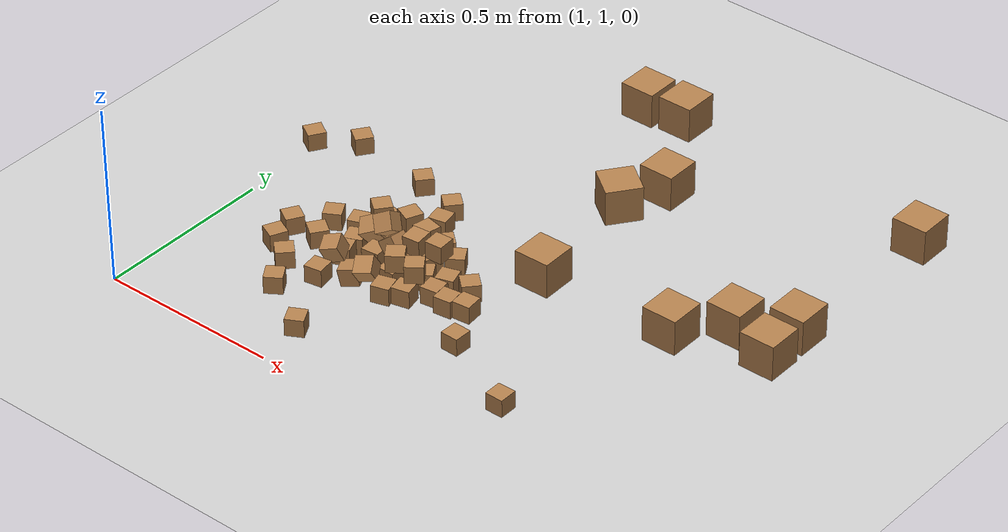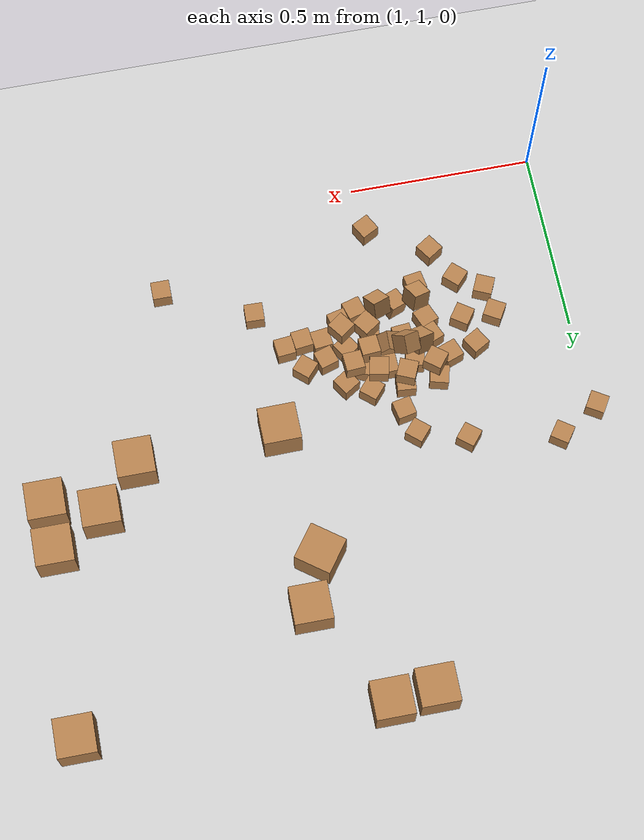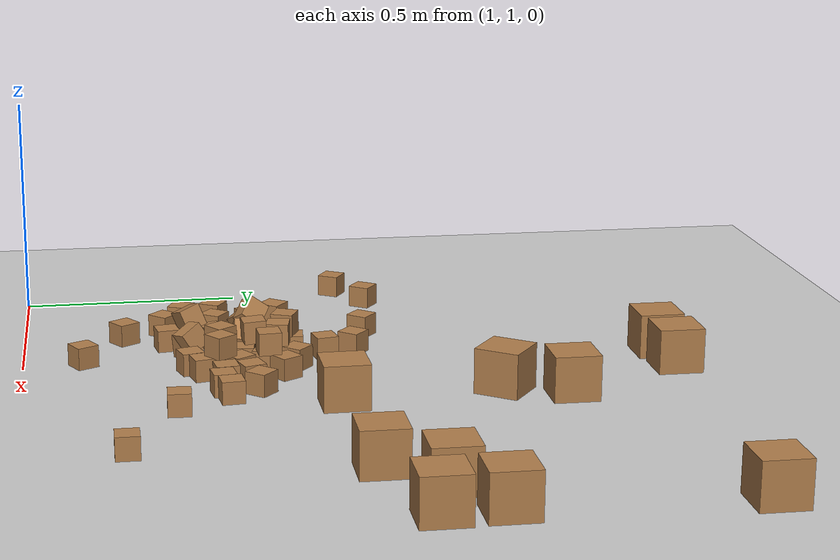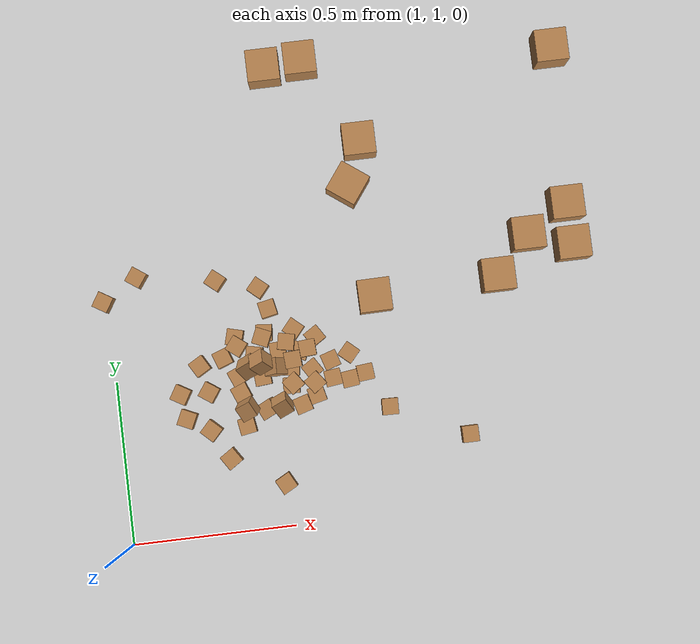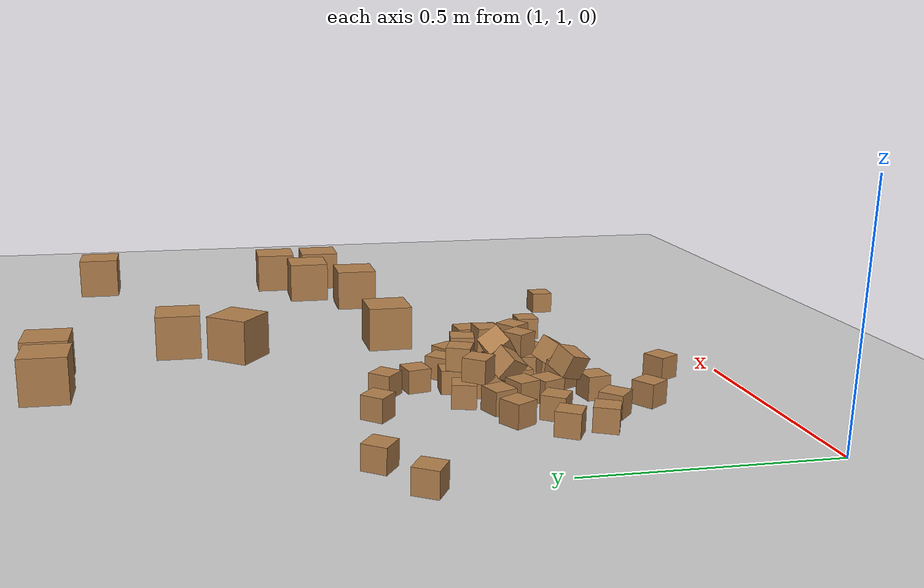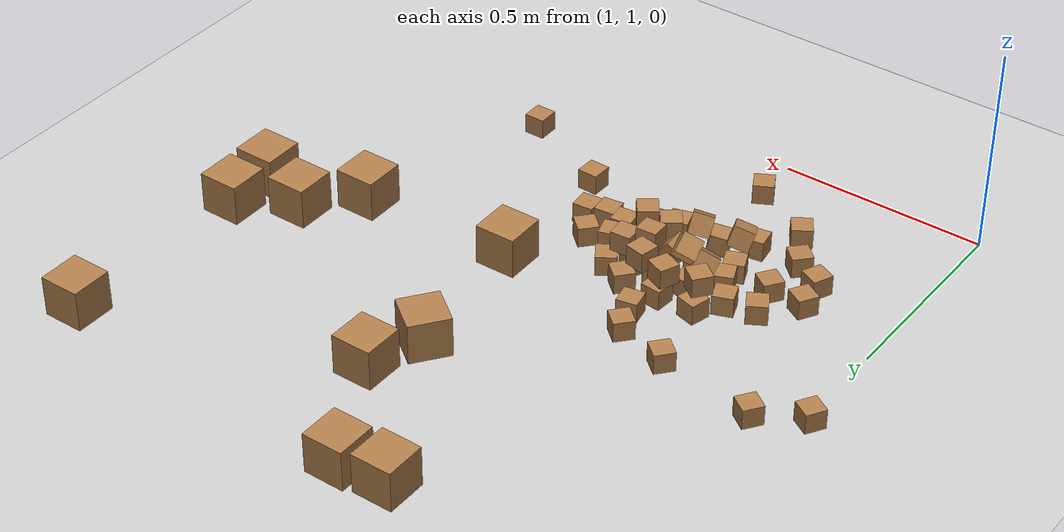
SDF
<sdf version="1.6">
 <world name="default">
  <light name="sun" type="directional">
   <pose>0 0 10 0 -0 0</pose>
   <diffuse>0.8 0.8 0.8 1</diffuse>
   <specular>0.2 0.2 0.2 1</specular>
   <attenuation>
    <range>100</range>
    <constant>0.9</constant>
    <linear>0.01</linear>
    <quadratic>0.01</quadratic>
   </attenuation>
   <direction>-0.5 0.1 -0.9</direction>
  </light>
  <model name="ground_plane">
   <static>1</static>
   <link name="link">
    <collision name="collision">
     <geometry><plane><normal>0 0 1</normal><size>100 100</size></plane></geometry>
     <surface>
      <contact><collide_bitmask>65535</collide_bitmask></contact>
      <friction><ode><mu>100</mu><mu2>50</mu2></ode></friction>
     </surface>
    </collision>
    <visual name="visual">
     <cast_shadows>0</cast_shadows>
     <geometry><plane><normal>0 0 1</normal><size>100 100</size></plane></geometry>
     <material>
      <script><uri>file://media/materials/scripts/gazebo.material</uri><name>Gazebo/Grey</name></script>
     </material>
    </visual>
   </link>
  </model>
  <gravity>0 0 -9.8</gravity>
  <magnetic_field>6e-06 2.3e-05 -4.2e-05</magnetic_field>
  <atmosphere type="adiabatic"/>
  <physics name="default_physics" default="0" type="ode">
   <max_step_size>0.001</max_step_size>
   <real_time_factor>1</real_time_factor>
   <real_time_update_rate>1000</real_time_update_rate>
  </physics>
  <scene><ambient>0.4 0.4 0.4 1</ambient><background>0.7 0.7 0.7 1</background><shadows>1</shadows></scene>
  <audio><device>default</device></audio>
  <spherical_coordinates>
   <surface_model>EARTH_WGS84</surface_model>
   <latitude_deg>0</latitude_deg>
   <longitude_deg>0</longitude_deg>
   <elevation>0</elevation>
   <heading_deg>0</heading_deg>
  </spherical_coordinates>
  <model name="cube_0487_10p0cm">
   <link name="link">
    <pose>0 0 0.05 0 -0 0</pose>
    <inertial>
     <mass>0.5167</mass>
     <inertia>
      <ixx>0.000861167</ixx>
      <ixy>0</ixy>
      <ixz>0</ixz>
      <iyy>0.000861167</iyy>
      <iyz>0</iyz>
      <izz>0.000861167</izz>
     </inertia>
    </inertial>
    <collision name="collision">
     <geometry><box><size>0.1 0.1 0.1</size></box></geometry>
     <surface>
      <contact>
       <poissons_ratio>0.347</poissons_ratio>
       <elastic_modulus>8.8e+09</elastic_modulus>
       <ode><kp>100000</kp><kd>100</kd><max_vel>100</max_vel><min_depth>0.001</min_depth></ode>
      </contact>
      <friction>
       <torsional>
        <coefficient>1</coefficient>
        <use_patch_radius>0</use_patch_radius>
        <surface_radius>0.01</surface_radius>
       </torsional>
      </friction>
     </surface>
    </collision>
    <visual name="visual">
     <geometry><box><size>0.1 0.1 0.1</size></box></geometry>
     <material>
      <script><uri>file://media/materials/scripts/gazebo.material</uri><name>Gazebo/Wood</name></script>
     </material>
    </visual>
   </link>
   <pose>2.4439 1.8834 -0.001013 0 -0 0</pose>
  </model>
  <model name="cube_0747_10p0cm">
   <link name="link">
    <pose>0 0 0.05 0 -0 0</pose>
    <inertial>
     <mass>0.5167</mass>
     <inertia>
      <ixx>0.000861167</ixx>
      <ixy>0</ixy>
      <ixz>0</ixz>
      <iyy>0.000861167</iyy>
      <iyz>0</iyz>
      <izz>0.000861167</izz>
     </inertia>
    </inertial>
    <collision name="collision">
     <geometry><box><size>0.1 0.1 0.1</size></box></geometry>
     <surface>
      <contact>
       <poissons_ratio>0.347</poissons_ratio>
       <elastic_modulus>8.8e+09</elastic_modulus>
       <ode><kp>100000</kp><kd>100</kd><max_vel>100</max_vel><min_depth>0.001</min_depth></ode>
      </contact>
      <friction>
       <torsional>
        <coefficient>1</coefficient>
        <use_patch_radius>0</use_patch_radius>
        <surface_radius>0.01</surface_radius>
       </torsional>
      </friction>
     </surface>
    </collision>
    <visual name="visual">
     <geometry><box><size>0.1 0.1 0.1</size></box></geometry>
     <material>
      <script><uri>file://media/materials/scripts/gazebo.material</uri><name>Gazebo/Wood</name></script>
     </material>
    </visual>
   </link>
   <pose>1.67955 2.42645 -0.001013 0 -0 0</pose>
  </model>
  <model name="cube_0038_10p0cm">
   <link name="link">
    <pose>0 0 0.05 0 -0 0</pose>
    <inertial>
     <mass>0.5167</mass>
     <inertia>
      <ixx>0.000861167</ixx>
      <ixy>0</ixy>
      <ixz>0</ixz>
      <iyy>0.000861167</iyy>
      <iyz>0</iyz>
      <izz>0.000861167</izz>
     </inertia>
    </inertial>
    <collision name="collision">
     <geometry><box><size>0.1 0.1 0.1</size></box></geometry>
     <surface>
      <contact>
       <poissons_ratio>0.347</poissons_ratio>
       <elastic_modulus>8.8e+09</elastic_modulus>
       <ode><kp>100000</kp><kd>100</kd><max_vel>100</max_vel><min_depth>0.001</min_depth></ode>
      </contact>
      <friction>
       <torsional>
        <coefficient>1</coefficient>
        <use_patch_radius>0</use_patch_radius>
        <surface_radius>0.01</surface_radius>
       </torsional>
      </friction>
     </surface>
    </collision>
    <visual name="visual">
     <geometry><box><size>0.1 0.1 0.1</size></box></geometry>
     <material>
      <script><uri>file://media/materials/scripts/gazebo.material</uri><name>Gazebo/Wood</name></script>
     </material>
    </visual>
   </link>
   <pose>1.56399 2.41632 -0.001013 0 -0 0</pose>
  </model>
  <model name="cube_0555_10p0cm">
   <link name="link">
    <pose>0 0 0.05 0 -0 0</pose>
    <inertial>
     <mass>0.5167</mass>
     <inertia>
      <ixx>0.000861167</ixx>
      <ixy>0</ixy>
      <ixz>0</ixz>
      <iyy>0.000861167</iyy>
      <iyz>0</iyz>
      <izz>0.000861167</izz>
     </inertia>
    </inertial>
    <collision name="collision">
     <geometry><box><size>0.1 0.1 0.1</size></box></geometry>
     <surface>
      <contact>
       <poissons_ratio>0.347</poissons_ratio>
       <elastic_modulus>8.8e+09</elastic_modulus>
       <ode><kp>100000</kp><kd>100</kd><max_vel>100</max_vel><min_depth>0.001</min_depth></ode>
      </contact>
      <friction>
       <torsional>
        <coefficient>1</coefficient>
        <use_patch_radius>0</use_patch_radius>
        <surface_radius>0.01</surface_radius>
       </torsional>
      </friction>
     </surface>
    </collision>
    <visual name="visual">
     <geometry><box><size>0.1 0.1 0.1</size></box></geometry>
     <material>
      <script><uri>file://media/materials/scripts/gazebo.material</uri><name>Gazebo/Wood</name></script>
     </material>
    </visual>
   </link>
   <pose>2.31334 1.80392 -0.001013 0 -0 0</pose>
  </model>
  <model name="cube_0059_10p0cm">
   <link name="link">
    <pose>0 0 0.05 0 -0 0</pose>
    <inertial>
     <mass>0.5167</mass>
     <inertia>
      <ixx>0.000861167</ixx>
      <ixy>0</ixy>
      <ixz>0</ixz>
      <iyy>0.000861167</iyy>
      <iyz>0</iyz>
      <izz>0.000861167</izz>
     </inertia>
    </inertial>
    <collision name="collision">
     <geometry><box><size>0.1 0.1 0.1</size></box></geometry>
     <surface>
      <contact>
       <poissons_ratio>0.347</poissons_ratio>
       <elastic_modulus>8.8e+09</elastic_modulus>
       <ode><kp>100000</kp><kd>100</kd><max_vel>100</max_vel><min_depth>0.001</min_depth></ode>
      </contact>
      <friction>
       <torsional>
        <coefficient>1</coefficient>
        <use_patch_radius>0</use_patch_radius>
        <surface_radius>0.01</surface_radius>
       </torsional>
      </friction>
     </surface>
    </collision>
    <visual name="visual">
     <geometry><box><size>0.1 0.1 0.1</size></box></geometry>
     <material>
      <script><uri>file://media/materials/scripts/gazebo.material</uri><name>Gazebo/Wood</name></script>
     </material>
    </visual>
   </link>
   <pose>1.83166 2.15412 -0.001013 0 0 -0.000922</pose>
  </model>
  <model name="cube_0230_10p0cm">
   <link name="link">
    <pose>0 0 0.05 0 -0 0</pose>
    <inertial>
     <mass>0.5167</mass>
     <inertia>
      <ixx>0.000861167</ixx>
      <ixy>0</ixy>
      <ixz>0</ixz>
      <iyy>0.000861167</iyy>
      <iyz>0</iyz>
      <izz>0.000861167</izz>
     </inertia>
    </inertial>
    <collision name="collision">
     <geometry><box><size>0.1 0.1 0.1</size></box></geometry>
     <surface>
      <contact>
       <poissons_ratio>0.347</poissons_ratio>
       <elastic_modulus>8.8e+09</elastic_modulus>
       <ode><kp>100000</kp><kd>100</kd><max_vel>100</max_vel><min_depth>0.001</min_depth></ode>
      </contact>
      <friction>
       <torsional>
        <coefficient>1</coefficient>
        <use_patch_radius>0</use_patch_radius>
        <surface_radius>0.01</surface_radius>
       </torsional>
      </friction>
     </surface>
    </collision>
    <visual name="visual">
     <geometry><box><size>0.1 0.1 0.1</size></box></geometry>
     <material>
      <script><uri>file://media/materials/scripts/gazebo.material</uri><name>Gazebo/Wood</name></script>
     </material>
    </visual>
   </link>
   <pose>2.44741 1.75877 -0.001013 0 -0 0</pose>
  </model>
  <model name="cube_0076_10p0cm">
   <link name="link">
    <pose>0 0 0.05 0 -0 0</pose>
    <inertial>
     <mass>0.5167</mass>
     <inertia>
      <ixx>0.000861167</ixx>
      <ixy>0</ixy>
      <ixz>0</ixz>
      <iyy>0.000861167</iyy>
      <iyz>0</iyz>
      <izz>0.000861167</izz>
     </inertia>
    </inertial>
    <collision name="collision">
     <geometry><box><size>0.1 0.1 0.1</size></box></geometry>
     <surface>
      <contact>
       <poissons_ratio>0.347</poissons_ratio>
       <elastic_modulus>8.8e+09</elastic_modulus>
       <ode><kp>100000</kp><kd>100</kd><max_vel>100</max_vel><min_depth>0.001</min_depth></ode>
      </contact>
      <friction>
       <torsional>
        <coefficient>1</coefficient>
        <use_patch_radius>0</use_patch_radius>
        <surface_radius>0.01</surface_radius>
       </torsional>
      </friction>
     </surface>
    </collision>
    <visual name="visual">
     <geometry><box><size>0.1 0.1 0.1</size></box></geometry>
     <material>
      <script><uri>file://media/materials/scripts/gazebo.material</uri><name>Gazebo/Wood</name></script>
     </material>
    </visual>
   </link>
   <pose>2.20626 1.68875 -0.001013 0 -0 0</pose>
  </model>
  <model name="cube_0741_10p0cm">
   <link name="link">
    <pose>0 0 0.05 0 -0 0</pose>
    <inertial>
     <mass>0.5167</mass>
     <inertia>
      <ixx>0.000861167</ixx>
      <ixy>0</ixy>
      <ixz>0</ixz>
      <iyy>0.000861167</iyy>
      <iyz>0</iyz>
      <izz>0.000861167</izz>
     </inertia>
    </inertial>
    <collision name="collision">
     <geometry><box><size>0.1 0.1 0.1</size></box></geometry>
     <surface>
      <contact>
       <poissons_ratio>0.347</poissons_ratio>
       <elastic_modulus>8.8e+09</elastic_modulus>
       <ode><kp>100000</kp><kd>100</kd><max_vel>100</max_vel><min_depth>0.001</min_depth></ode>
      </contact>
      <friction>
       <torsional>
        <coefficient>1</coefficient>
        <use_patch_radius>0</use_patch_radius>
        <surface_radius>0.01</surface_radius>
       </torsional>
      </friction>
     </surface>
    </collision>
    <visual name="visual">
     <geometry><box><size>0.1 0.1 0.1</size></box></geometry>
     <material>
      <script><uri>file://media/materials/scripts/gazebo.material</uri><name>Gazebo/Wood</name></script>
     </material>
    </visual>
   </link>
   <pose>2.4582 2.37258 -0.001013 0 -0 0</pose>
  </model>
  <model name="cube_0599_10p0cm">
   <link name="link">
    <pose>0 0 0.05 0 -0 0</pose>
    <inertial>
     <mass>0.5167</mass>
     <inertia>
      <ixx>0.000861167</ixx>
      <ixy>0</ixy>
      <ixz>0</ixz>
      <iyy>0.000861167</iyy>
      <iyz>0</iyz>
      <izz>0.000861167</izz>
     </inertia>
    </inertial>
    <collision name="collision">
     <geometry><box><size>0.1 0.1 0.1</size></box></geometry>
     <surface>
      <contact>
       <poissons_ratio>0.347</poissons_ratio>
       <elastic_modulus>8.8e+09</elastic_modulus>
       <ode><kp>100000</kp><kd>100</kd><max_vel>100</max_vel><min_depth>0.001</min_depth></ode>
      </contact>
      <friction>
       <torsional>
        <coefficient>1</coefficient>
        <use_patch_radius>0</use_patch_radius>
        <surface_radius>0.01</surface_radius>
       </torsional>
      </friction>
     </surface>
    </collision>
    <visual name="visual">
     <geometry><box><size>0.1 0.1 0.1</size></box></geometry>
     <material>
      <script><uri>file://media/materials/scripts/gazebo.material</uri><name>Gazebo/Wood</name></script>
     </material>
    </visual>
   </link>
   <pose>1.82292 1.66964 -0.001013 0 -0 0.014042</pose>
  </model>
  <model name="cube_0356_10p0cm">
   <link name="link">
    <pose>0 0 0.05 0 -0 0</pose>
    <inertial>
     <mass>0.5167</mass>
     <inertia>
      <ixx>0.000861167</ixx>
      <ixy>0</ixy>
      <ixz>0</ixz>
      <iyy>0.000861167</iyy>
      <iyz>0</iyz>
      <izz>0.000861167</izz>
     </inertia>
    </inertial>
    <collision name="collision">
     <geometry><box><size>0.1 0.1 0.1</size></box></geometry>
     <surface>
      <contact>
       <poissons_ratio>0.347</poissons_ratio>
       <elastic_modulus>8.8e+09</elastic_modulus>
       <ode><kp>100000</kp><kd>100</kd><max_vel>100</max_vel><min_depth>0.001</min_depth></ode>
      </contact>
      <friction>
       <torsional>
        <coefficient>1</coefficient>
        <use_patch_radius>0</use_patch_radius>
        <surface_radius>0.01</surface_radius>
       </torsional>
      </friction>
     </surface>
    </collision>
    <visual name="visual">
     <geometry><box><size>0.1 0.1 0.1</size></box></geometry>
     <material>
      <script><uri>file://media/materials/scripts/gazebo.material</uri><name>Gazebo/Wood</name></script>
     </material>
    </visual>
   </link>
   <pose>1.74197 2.04983 0.048987 1.5708 -0 0.936336</pose>
  </model>
  <model name="cube_0233_05p0cm">
   <link name="link">
    <pose>0 0 0.025 0 -0 0</pose>
    <inertial>
     <mass>0.0565</mass>
     <inertia>
      <ixx>2.35417e-05</ixx>
      <ixy>0</ixy>
      <ixz>0</ixz>
      <iyy>2.35417e-05</iyy>
      <iyz>0</iyz>
      <izz>2.35417e-05</izz>
     </inertia>
    </inertial>
    <collision name="collision">
     <geometry><box><size>0.05 0.05 0.05</size></box></geometry>
     <surface>
      <contact>
       <poissons_ratio>0.347</poissons_ratio>
       <elastic_modulus>8.8e+09</elastic_modulus>
       <ode><kp>100000</kp><kd>1</kd><max_vel>1</max_vel><min_depth>0.001</min_depth></ode>
      </contact>
      <friction>
       <torsional>
        <coefficient>1</coefficient>
        <use_patch_radius>0</use_patch_radius>
        <surface_radius>0.05</surface_radius>
       </torsional>
      </friction>
     </surface>
    </collision>
    <visual name="visual">
     <geometry><box><size>0.05 0.05 0.05</size></box></geometry>
     <material>
      <script><uri>file://media/materials/scripts/gazebo.material</uri><name>Gazebo/Wood</name></script>
     </material>
    </visual>
   </link>
   <pose>1.53731 1.42735 -0.001003 -5e-05 4.8e-05 -0.014811</pose>
  </model>
  <model name="cube_0399_05p0cm">
   <link name="link">
    <pose>0 0 0.025 0 -0 0</pose>
    <inertial>
     <mass>0.0565</mass>
     <inertia>
      <ixx>2.35417e-05</ixx>
      <ixy>0</ixy>
      <ixz>0</ixz>
      <iyy>2.35417e-05</iyy>
      <iyz>0</iyz>
      <izz>2.35417e-05</izz>
     </inertia>
    </inertial>
    <collision name="collision">
     <geometry><box><size>0.05 0.05 0.05</size></box></geometry>
     <surface>
      <contact>
       <poissons_ratio>0.347</poissons_ratio>
       <elastic_modulus>8.8e+09</elastic_modulus>
       <ode><kp>100000</kp><kd>1</kd><max_vel>1</max_vel><min_depth>0.001</min_depth></ode>
      </contact>
      <friction>
       <torsional>
        <coefficient>1</coefficient>
        <use_patch_radius>0</use_patch_radius>
        <surface_radius>0.05</surface_radius>
       </torsional>
      </friction>
     </surface>
    </collision>
    <visual name="visual">
     <geometry><box><size>0.05 0.05 0.05</size></box></geometry>
     <material>
      <script><uri>file://media/materials/scripts/gazebo.material</uri><name>Gazebo/Wood</name></script>
     </material>
    </visual>
   </link>
   <pose>1.74273 1.43775 0.023999 2.7967 1.57079 2.89628</pose>
  </model>
  <model name="cube_0844_05p0cm">
   <link name="link">
    <pose>0 0 0.025 0 -0 0</pose>
    <inertial>
     <mass>0.0565</mass>
     <inertia>
      <ixx>2.35417e-05</ixx>
      <ixy>0</ixy>
      <ixz>0</ixz>
      <iyy>2.35417e-05</iyy>
      <iyz>0</iyz>
      <izz>2.35417e-05</izz>
     </inertia>
    </inertial>
    <collision name="collision">
     <geometry><box><size>0.05 0.05 0.05</size></box></geometry>
     <surface>
      <contact>
       <poissons_ratio>0.347</poissons_ratio>
       <elastic_modulus>8.8e+09</elastic_modulus>
       <ode><kp>100000</kp><kd>1</kd><max_vel>1</max_vel><min_depth>0.001</min_depth></ode>
      </contact>
      <friction>
       <torsional>
        <coefficient>1</coefficient>
        <use_patch_radius>0</use_patch_radius>
        <surface_radius>0.05</surface_radius>
       </torsional>
      </friction>
     </surface>
    </collision>
    <visual name="visual">
     <geometry><box><size>0.05 0.05 0.05</size></box></geometry>
     <material>
      <script><uri>file://media/materials/scripts/gazebo.material</uri><name>Gazebo/Wood</name></script>
     </material>
    </visual>
   </link>
   <pose>1.45237 1.46277 -0.001003 1.4e-05 -2.9e-05 0.090534</pose>
  </model>
  <model name="cube_0829_05p0cm">
   <link name="link">
    <pose>0 0 0.025 0 -0 0</pose>
    <inertial>
     <mass>0.0565</mass>
     <inertia>
      <ixx>2.35417e-05</ixx>
      <ixy>0</ixy>
      <ixz>0</ixz>
      <iyy>2.35417e-05</iyy>
      <iyz>0</iyz>
      <izz>2.35417e-05</izz>
     </inertia>
    </inertial>
    <collision name="collision">
     <geometry><box><size>0.05 0.05 0.05</size></box></geometry>
     <surface>
      <contact>
       <poissons_ratio>0.347</poissons_ratio>
       <elastic_modulus>8.8e+09</elastic_modulus>
       <ode><kp>100000</kp><kd>1</kd><max_vel>1</max_vel><min_depth>0.001</min_depth></ode>
      </contact>
      <friction>
       <torsional>
        <coefficient>1</coefficient>
        <use_patch_radius>0</use_patch_radius>
        <surface_radius>0.05</surface_radius>
       </torsional>
      </friction>
     </surface>
    </collision>
    <visual name="visual">
     <geometry><box><size>0.05 0.05 0.05</size></box></geometry>
     <material>
      <script><uri>file://media/materials/scripts/gazebo.material</uri><name>Gazebo/Wood</name></script>
     </material>
    </visual>
   </link>
   <pose>1.53986 1.45746 0.023996 -1.57079 -9e-06 -0.148982</pose>
  </model>
  <model name="cube_0493_05p0cm">
   <link name="link">
    <pose>0 0 0.025 0 -0 0</pose>
    <inertial>
     <mass>0.0565</mass>
     <inertia>
      <ixx>2.35417e-05</ixx>
      <ixy>0</ixy>
      <ixz>0</ixz>
      <iyy>2.35417e-05</iyy>
      <iyz>0</iyz>
      <izz>2.35417e-05</izz>
     </inertia>
    </inertial>
    <collision name="collision">
     <geometry><box><size>0.05 0.05 0.05</size></box></geometry>
     <surface>
      <contact>
       <poissons_ratio>0.347</poissons_ratio>
       <elastic_modulus>8.8e+09</elastic_modulus>
       <ode><kp>100000</kp><kd>1</kd><max_vel>1</max_vel><min_depth>0.001</min_depth></ode>
      </contact>
      <friction>
       <torsional>
        <coefficient>1</coefficient>
        <use_patch_radius>0</use_patch_radius>
        <surface_radius>0.05</surface_radius>
       </torsional>
      </friction>
     </surface>
    </collision>
    <visual name="visual">
     <geometry><box><size>0.05 0.05 0.05</size></box></geometry>
     <material>
      <script><uri>file://media/materials/scripts/gazebo.material</uri><name>Gazebo/Wood</name></script>
     </material>
    </visual>
   </link>
   <pose>1.46921 1.34229 0.028546 -1.57068 -0.204429 0.449199</pose>
  </model>
  <model name="cube_0588_05p0cm">
   <link name="link">
    <pose>0 0 0.025 0 -0 0</pose>
    <inertial>
     <mass>0.0565</mass>
     <inertia>
      <ixx>2.35417e-05</ixx>
      <ixy>0</ixy>
      <ixz>0</ixz>
      <iyy>2.35417e-05</iyy>
      <iyz>0</iyz>
      <izz>2.35417e-05</izz>
     </inertia>
    </inertial>
    <collision name="collision">
     <geometry><box><size>0.05 0.05 0.05</size></box></geometry>
     <surface>
      <contact>
       <poissons_ratio>0.347</poissons_ratio>
       <elastic_modulus>8.8e+09</elastic_modulus>
       <ode><kp>100000</kp><kd>1</kd><max_vel>1</max_vel><min_depth>0.001</min_depth></ode>
      </contact>
      <friction>
       <torsional>
        <coefficient>1</coefficient>
        <use_patch_radius>0</use_patch_radius>
        <surface_radius>0.05</surface_radius>
       </torsional>
      </friction>
     </surface>
    </collision>
    <visual name="visual">
     <geometry><box><size>0.05 0.05 0.05</size></box></geometry>
     <material>
      <script><uri>file://media/materials/scripts/gazebo.material</uri><name>Gazebo/Wood</name></script>
     </material>
    </visual>
   </link>
   <pose>1.43353 1.53398 -0.000736 -0.000105 -0.010819 -0.211148</pose>
  </model>
  <model name="cube_0846_05p0cm">
   <link name="link">
    <pose>0 0 0.025 0 -0 0</pose>
    <inertial>
     <mass>0.0565</mass>
     <inertia>
      <ixx>2.35417e-05</ixx>
      <ixy>0</ixy>
      <ixz>0</ixz>
      <iyy>2.35417e-05</iyy>
      <iyz>0</iyz>
      <izz>2.35417e-05</izz>
     </inertia>
    </inertial>
    <collision name="collision">
     <geometry><box><size>0.05 0.05 0.05</size></box></geometry>
     <surface>
      <contact>
       <poissons_ratio>0.347</poissons_ratio>
       <elastic_modulus>8.8e+09</elastic_modulus>
       <ode><kp>100000</kp><kd>1</kd><max_vel>1</max_vel><min_depth>0.001</min_depth></ode>
      </contact>
      <friction>
       <torsional>
        <coefficient>1</coefficient>
        <use_patch_radius>0</use_patch_radius>
        <surface_radius>0.05</surface_radius>
       </torsional>
      </friction>
     </surface>
    </collision>
    <visual name="visual">
     <geometry><box><size>0.05 0.05 0.05</size></box></geometry>
     <material>
      <script><uri>file://media/materials/scripts/gazebo.material</uri><name>Gazebo/Wood</name></script>
     </material>
    </visual>
   </link>
   <pose>1.44932 1.75408 0.023999 1.5708 -0 0.853521</pose>
  </model>
  <model name="cube_0293_05p0cm">
   <link name="link">
    <pose>0 0 0.025 0 -0 0</pose>
    <inertial>
     <mass>0.0565</mass>
     <inertia>
      <ixx>2.35417e-05</ixx>
      <ixy>0</ixy>
      <ixz>0</ixz>
      <iyy>2.35417e-05</iyy>
      <iyz>0</iyz>
      <izz>2.35417e-05</izz>
     </inertia>
    </inertial>
    <collision name="collision">
     <geometry><box><size>0.05 0.05 0.05</size></box></geometry>
     <surface>
      <contact>
       <poissons_ratio>0.347</poissons_ratio>
       <elastic_modulus>8.8e+09</elastic_modulus>
       <ode><kp>100000</kp><kd>1</kd><max_vel>1</max_vel><min_depth>0.001</min_depth></ode>
      </contact>
      <friction>
       <torsional>
        <coefficient>1</coefficient>
        <use_patch_radius>0</use_patch_radius>
        <surface_radius>0.05</surface_radius>
       </torsional>
      </friction>
     </surface>
    </collision>
    <visual name="visual">
     <geometry><box><size>0.05 0.05 0.05</size></box></geometry>
     <material>
      <script><uri>file://media/materials/scripts/gazebo.material</uri><name>Gazebo/Wood</name></script>
     </material>
    </visual>
   </link>
   <pose>1.47107 1.59783 -0.001002 2.8e-05 -1.5e-05 -0.078631</pose>
  </model>
  <model name="cube_0204_05p0cm">
   <link name="link">
    <pose>0 0 0.025 0 -0 0</pose>
    <inertial>
     <mass>0.0565</mass>
     <inertia>
      <ixx>2.35417e-05</ixx>
      <ixy>0</ixy>
      <ixz>0</ixz>
      <iyy>2.35417e-05</iyy>
      <iyz>0</iyz>
      <izz>2.35417e-05</izz>
     </inertia>
    </inertial>
    <collision name="collision">
     <geometry><box><size>0.05 0.05 0.05</size></box></geometry>
     <surface>
      <contact>
       <poissons_ratio>0.347</poissons_ratio>
       <elastic_modulus>8.8e+09</elastic_modulus>
       <ode><kp>100000</kp><kd>1</kd><max_vel>1</max_vel><min_depth>0.001</min_depth></ode>
      </contact>
      <friction>
       <torsional>
        <coefficient>1</coefficient>
        <use_patch_radius>0</use_patch_radius>
        <surface_radius>0.05</surface_radius>
       </torsional>
      </friction>
     </surface>
    </collision>
    <visual name="visual">
     <geometry><box><size>0.05 0.05 0.05</size></box></geometry>
     <material>
      <script><uri>file://media/materials/scripts/gazebo.material</uri><name>Gazebo/Wood</name></script>
     </material>
    </visual>
   </link>
   <pose>1.50842 1.53937 -0.001002 -4.7e-05 3e-06 0.033762</pose>
  </model>
  <model name="cube_0288_05p0cm">
   <link name="link">
    <pose>0 0 0.025 0 -0 0</pose>
    <inertial>
     <mass>0.0565</mass>
     <inertia>
      <ixx>2.35417e-05</ixx>
      <ixy>0</ixy>
      <ixz>0</ixz>
      <iyy>2.35417e-05</iyy>
      <iyz>0</iyz>
      <izz>2.35417e-05</izz>
     </inertia>
    </inertial>
    <collision name="collision">
     <geometry><box><size>0.05 0.05 0.05</size></box></geometry>
     <surface>
      <contact>
       <poissons_ratio>0.347</poissons_ratio>
       <elastic_modulus>8.8e+09</elastic_modulus>
       <ode><kp>100000</kp><kd>1</kd><max_vel>1</max_vel><min_depth>0.001</min_depth></ode>
      </contact>
      <friction>
       <torsional>
        <coefficient>1</coefficient>
        <use_patch_radius>0</use_patch_radius>
        <surface_radius>0.05</surface_radius>
       </torsional>
      </friction>
     </surface>
    </collision>
    <visual name="visual">
     <geometry><box><size>0.05 0.05 0.05</size></box></geometry>
     <material>
      <script><uri>file://media/materials/scripts/gazebo.material</uri><name>Gazebo/Wood</name></script>
     </material>
    </visual>
   </link>
   <pose>1.83016 1.32753 0.048999 3.14159 0 3.11461</pose>
  </model>
  <model name="cube_0947_05p0cm">
   <link name="link">
    <pose>0 0 0.025 0 -0 0</pose>
    <inertial>
     <mass>0.0565</mass>
     <inertia>
      <ixx>2.35417e-05</ixx>
      <ixy>0</ixy>
      <ixz>0</ixz>
      <iyy>2.35417e-05</iyy>
      <iyz>0</iyz>
      <izz>2.35417e-05</izz>
     </inertia>
    </inertial>
    <collision name="collision">
     <geometry><box><size>0.05 0.05 0.05</size></box></geometry>
     <surface>
      <contact>
       <poissons_ratio>0.347</poissons_ratio>
       <elastic_modulus>8.8e+09</elastic_modulus>
       <ode><kp>100000</kp><kd>1</kd><max_vel>1</max_vel><min_depth>0.001</min_depth></ode>
      </contact>
      <friction>
       <torsional>
        <coefficient>1</coefficient>
        <use_patch_radius>0</use_patch_radius>
        <surface_radius>0.05</surface_radius>
       </torsional>
      </friction>
     </surface>
    </collision>
    <visual name="visual">
     <geometry><box><size>0.05 0.05 0.05</size></box></geometry>
     <material>
      <script><uri>file://media/materials/scripts/gazebo.material</uri><name>Gazebo/Wood</name></script>
     </material>
    </visual>
   </link>
   <pose>1.60421 1.55578 0.023998 2.43341 1.57077 3.00236</pose>
  </model>
  <model name="cube_0254_05p0cm">
   <link name="link">
    <pose>0 0 0.025 0 -0 0</pose>
    <inertial>
     <mass>0.0565</mass>
     <inertia>
      <ixx>2.35417e-05</ixx>
      <ixy>0</ixy>
      <ixz>0</ixz>
      <iyy>2.35417e-05</iyy>
      <iyz>0</iyz>
      <izz>2.35417e-05</izz>
     </inertia>
    </inertial>
    <collision name="collision">
     <geometry><box><size>0.05 0.05 0.05</size></box></geometry>
     <surface>
      <contact>
       <poissons_ratio>0.347</poissons_ratio>
       <elastic_modulus>8.8e+09</elastic_modulus>
       <ode><kp>100000</kp><kd>1</kd><max_vel>1</max_vel><min_depth>0.001</min_depth></ode>
      </contact>
      <friction>
       <torsional>
        <coefficient>1</coefficient>
        <use_patch_radius>0</use_patch_radius>
        <surface_radius>0.05</surface_radius>
       </torsional>
      </friction>
     </surface>
    </collision>
    <visual name="visual">
     <geometry><box><size>0.05 0.05 0.05</size></box></geometry>
     <material>
      <script><uri>file://media/materials/scripts/gazebo.material</uri><name>Gazebo/Wood</name></script>
     </material>
    </visual>
   </link>
   <pose>1.27817 1.31897 -0.001001 0 0 -0.755856</pose>
  </model>
  <model name="cube_0472_05p0cm">
   <link name="link">
    <pose>0 0 0.025 0 -0 0</pose>
    <inertial>
     <mass>0.0565</mass>
     <inertia>
      <ixx>2.35417e-05</ixx>
      <ixy>0</ixy>
      <ixz>0</ixz>
      <iyy>2.35417e-05</iyy>
      <iyz>0</iyz>
      <izz>2.35417e-05</izz>
     </inertia>
    </inertial>
    <collision name="collision">
     <geometry><box><size>0.05 0.05 0.05</size></box></geometry>
     <surface>
      <contact>
       <poissons_ratio>0.347</poissons_ratio>
       <elastic_modulus>8.8e+09</elastic_modulus>
       <ode><kp>100000</kp><kd>1</kd><max_vel>1</max_vel><min_depth>0.001</min_depth></ode>
      </contact>
      <friction>
       <torsional>
        <coefficient>1</coefficient>
        <use_patch_radius>0</use_patch_radius>
        <surface_radius>0.05</surface_radius>
       </torsional>
      </friction>
     </surface>
    </collision>
    <visual name="visual">
     <geometry><box><size>0.05 0.05 0.05</size></box></geometry>
     <material>
      <script><uri>file://media/materials/scripts/gazebo.material</uri><name>Gazebo/Wood</name></script>
     </material>
    </visual>
   </link>
   <pose>1.20866 1.46051 0.023999 -2.10009 -1.57079 3.14159</pose>
  </model>
  <model name="cube_0798_05p0cm">
   <link name="link">
    <pose>0 0 0.025 0 -0 0</pose>
    <inertial>
     <mass>0.0565</mass>
     <inertia>
      <ixx>2.35417e-05</ixx>
      <ixy>0</ixy>
      <ixz>0</ixz>
      <iyy>2.35417e-05</iyy>
      <iyz>0</iyz>
      <izz>2.35417e-05</izz>
     </inertia>
    </inertial>
    <collision name="collision">
     <geometry><box><size>0.05 0.05 0.05</size></box></geometry>
     <surface>
      <contact>
       <poissons_ratio>0.347</poissons_ratio>
       <elastic_modulus>8.8e+09</elastic_modulus>
       <ode><kp>100000</kp><kd>1</kd><max_vel>1</max_vel><min_depth>0.001</min_depth></ode>
      </contact>
      <friction>
       <torsional>
        <coefficient>1</coefficient>
        <use_patch_radius>0</use_patch_radius>
        <surface_radius>0.05</surface_radius>
       </torsional>
      </friction>
     </surface>
    </collision>
    <visual name="visual">
     <geometry><box><size>0.05 0.05 0.05</size></box></geometry>
     <material>
      <script><uri>file://media/materials/scripts/gazebo.material</uri><name>Gazebo/Wood</name></script>
     </material>
    </visual>
   </link>
   <pose>1.4003 1.48438 0.024642 1.86455 -1.55377 -1.46869</pose>
  </model>
  <model name="cube_0718_05p0cm">
   <link name="link">
    <pose>0 0 0.025 0 -0 0</pose>
    <inertial>
     <mass>0.0565</mass>
     <inertia>
      <ixx>2.35417e-05</ixx>
      <ixy>0</ixy>
      <ixz>0</ixz>
      <iyy>2.35417e-05</iyy>
      <iyz>0</iyz>
      <izz>2.35417e-05</izz>
     </inertia>
    </inertial>
    <collision name="collision">
     <geometry><box><size>0.05 0.05 0.05</size></box></geometry>
     <surface>
      <contact>
       <poissons_ratio>0.347</poissons_ratio>
       <elastic_modulus>8.8e+09</elastic_modulus>
       <ode><kp>100000</kp><kd>1</kd><max_vel>1</max_vel><min_depth>0.001</min_depth></ode>
      </contact>
      <friction>
       <torsional>
        <coefficient>1</coefficient>
        <use_patch_radius>0</use_patch_radius>
        <surface_radius>0.05</surface_radius>
       </torsional>
      </friction>
     </surface>
    </collision>
    <visual name="visual">
     <geometry><box><size>0.05 0.05 0.05</size></box></geometry>
     <material>
      <script><uri>file://media/materials/scripts/gazebo.material</uri><name>Gazebo/Wood</name></script>
     </material>
    </visual>
   </link>
   <pose>1.49637 1.51333 0.058275 1.3794 0.873597 -0.157128</pose>
  </model>
  <model name="cube_0536_05p0cm">
   <link name="link">
    <pose>0 0 0.025 0 -0 0</pose>
    <inertial>
     <mass>0.0565</mass>
     <inertia>
      <ixx>2.35417e-05</ixx>
      <ixy>0</ixy>
      <ixz>0</ixz>
      <iyy>2.35417e-05</iyy>
      <iyz>0</iyz>
      <izz>2.35417e-05</izz>
     </inertia>
    </inertial>
    <collision name="collision">
     <geometry><box><size>0.05 0.05 0.05</size></box></geometry>
     <surface>
      <contact>
       <poissons_ratio>0.347</poissons_ratio>
       <elastic_modulus>8.8e+09</elastic_modulus>
       <ode><kp>100000</kp><kd>1</kd><max_vel>1</max_vel><min_depth>0.001</min_depth></ode>
      </contact>
      <friction>
       <torsional>
        <coefficient>1</coefficient>
        <use_patch_radius>0</use_patch_radius>
        <surface_radius>0.05</surface_radius>
       </torsional>
      </friction>
     </surface>
    </collision>
    <visual name="visual">
     <geometry><box><size>0.05 0.05 0.05</size></box></geometry>
     <material>
      <script><uri>file://media/materials/scripts/gazebo.material</uri><name>Gazebo/Wood</name></script>
     </material>
    </visual>
   </link>
   <pose>1.42658 1.48005 0.057531 -1.05224 -0.4378 0.388262</pose>
  </model>
  <model name="cube_0141_05p0cm">
   <link name="link">
    <pose>0 0 0.025 0 -0 0</pose>
    <inertial>
     <mass>0.0565</mass>
     <inertia>
      <ixx>2.35417e-05</ixx>
      <ixy>0</ixy>
      <ixz>0</ixz>
      <iyy>2.35417e-05</iyy>
      <iyz>0</iyz>
      <izz>2.35417e-05</izz>
     </inertia>
    </inertial>
    <collision name="collision">
     <geometry><box><size>0.05 0.05 0.05</size></box></geometry>
     <surface>
      <contact>
       <poissons_ratio>0.347</poissons_ratio>
       <elastic_modulus>8.8e+09</elastic_modulus>
       <ode><kp>100000</kp><kd>1</kd><max_vel>1</max_vel><min_depth>0.001</min_depth></ode>
      </contact>
      <friction>
       <torsional>
        <coefficient>1</coefficient>
        <use_patch_radius>0</use_patch_radius>
        <surface_radius>0.05</surface_radius>
       </torsional>
      </friction>
     </surface>
    </collision>
    <visual name="visual">
     <geometry><box><size>0.05 0.05 0.05</size></box></geometry>
     <material>
      <script><uri>file://media/materials/scripts/gazebo.material</uri><name>Gazebo/Wood</name></script>
     </material>
    </visual>
   </link>
   <pose>1.54601 1.58059 0.023998 -1.5708 -3.1e-05 -0.71114</pose>
  </model>
  <model name="cube_0855_05p0cm">
   <link name="link">
    <pose>0 0 0.025 0 -0 0</pose>
    <inertial>
     <mass>0.0565</mass>
     <inertia>
      <ixx>2.35417e-05</ixx>
      <ixy>0</ixy>
      <ixz>0</ixz>
      <iyy>2.35417e-05</iyy>
      <iyz>0</iyz>
      <izz>2.35417e-05</izz>
     </inertia>
    </inertial>
    <collision name="collision">
     <geometry><box><size>0.05 0.05 0.05</size></box></geometry>
     <surface>
      <contact>
       <poissons_ratio>0.347</poissons_ratio>
       <elastic_modulus>8.8e+09</elastic_modulus>
       <ode><kp>100000</kp><kd>1</kd><max_vel>1</max_vel><min_depth>0.001</min_depth></ode>
      </contact>
      <friction>
       <torsional>
        <coefficient>1</coefficient>
        <use_patch_radius>0</use_patch_radius>
        <surface_radius>0.05</surface_radius>
       </torsional>
      </friction>
     </surface>
    </collision>
    <visual name="visual">
     <geometry><box><size>0.05 0.05 0.05</size></box></geometry>
     <material>
      <script><uri>file://media/materials/scripts/gazebo.material</uri><name>Gazebo/Wood</name></script>
     </material>
    </visual>
   </link>
   <pose>1.5266 1.38137 0.063924 -1.9692 1.02043 1.63691</pose>
  </model>
  <model name="cube_0382_05p0cm">
   <link name="link">
    <pose>0 0 0.025 0 -0 0</pose>
    <inertial>
     <mass>0.0565</mass>
     <inertia>
      <ixx>2.35417e-05</ixx>
      <ixy>0</ixy>
      <ixz>0</ixz>
      <iyy>2.35417e-05</iyy>
      <iyz>0</iyz>
      <izz>2.35417e-05</izz>
     </inertia>
    </inertial>
    <collision name="collision">
     <geometry><box><size>0.05 0.05 0.05</size></box></geometry>
     <surface>
      <contact>
       <poissons_ratio>0.347</poissons_ratio>
       <elastic_modulus>8.8e+09</elastic_modulus>
       <ode><kp>100000</kp><kd>1</kd><max_vel>1</max_vel><min_depth>0.001</min_depth></ode>
      </contact>
      <friction>
       <torsional>
        <coefficient>1</coefficient>
        <use_patch_radius>0</use_patch_radius>
        <surface_radius>0.05</surface_radius>
       </torsional>
      </friction>
     </surface>
    </collision>
    <visual name="visual">
     <geometry><box><size>0.05 0.05 0.05</size></box></geometry>
     <material>
      <script><uri>file://media/materials/scripts/gazebo.material</uri><name>Gazebo/Wood</name></script>
     </material>
    </visual>
   </link>
   <pose>1.51272 1.56536 0.072996 0.09979 1.57076 -0.101741</pose>
  </model>
  <model name="cube_0270_05p0cm">
   <link name="link">
    <pose>0 0 0.025 0 -0 0</pose>
    <inertial>
     <mass>0.0565</mass>
     <inertia>
      <ixx>2.35417e-05</ixx>
      <ixy>0</ixy>
      <ixz>0</ixz>
      <iyy>2.35417e-05</iyy>
      <iyz>0</iyz>
      <izz>2.35417e-05</izz>
     </inertia>
    </inertial>
    <collision name="collision">
     <geometry><box><size>0.05 0.05 0.05</size></box></geometry>
     <surface>
      <contact>
       <poissons_ratio>0.347</poissons_ratio>
       <elastic_modulus>8.8e+09</elastic_modulus>
       <ode><kp>100000</kp><kd>1</kd><max_vel>1</max_vel><min_depth>0.001</min_depth></ode>
      </contact>
      <friction>
       <torsional>
        <coefficient>1</coefficient>
        <use_patch_radius>0</use_patch_radius>
        <surface_radius>0.05</surface_radius>
       </torsional>
      </friction>
     </surface>
    </collision>
    <visual name="visual">
     <geometry><box><size>0.05 0.05 0.05</size></box></geometry>
     <material>
      <script><uri>file://media/materials/scripts/gazebo.material</uri><name>Gazebo/Wood</name></script>
     </material>
    </visual>
   </link>
   <pose>1.61181 1.39052 0.048998 -3.14158 1.1e-05 1.8006</pose>
  </model>
  <model name="cube_0802_05p0cm">
   <link name="link">
    <pose>0 0 0.025 0 -0 0</pose>
    <inertial>
     <mass>0.0565</mass>
     <inertia>
      <ixx>2.35417e-05</ixx>
      <ixy>0</ixy>
      <ixz>0</ixz>
      <iyy>2.35417e-05</iyy>
      <iyz>0</iyz>
      <izz>2.35417e-05</izz>
     </inertia>
    </inertial>
    <collision name="collision">
     <geometry><box><size>0.05 0.05 0.05</size></box></geometry>
     <surface>
      <contact>
       <poissons_ratio>0.347</poissons_ratio>
       <elastic_modulus>8.8e+09</elastic_modulus>
       <ode><kp>100000</kp><kd>1</kd><max_vel>1</max_vel><min_depth>0.001</min_depth></ode>
      </contact>
      <friction>
       <torsional>
        <coefficient>1</coefficient>
        <use_patch_radius>0</use_patch_radius>
        <surface_radius>0.05</surface_radius>
       </torsional>
      </friction>
     </surface>
    </collision>
    <visual name="visual">
     <geometry><box><size>0.05 0.05 0.05</size></box></geometry>
     <material>
      <script><uri>file://media/materials/scripts/gazebo.material</uri><name>Gazebo/Wood</name></script>
     </material>
    </visual>
   </link>
   <pose>1.40468 1.43225 0.023998 -1.5708 -2.4e-05 1.95528</pose>
  </model>
  <model name="cube_0228_05p0cm">
   <link name="link">
    <pose>0 0 0.025 0 -0 0</pose>
    <inertial>
     <mass>0.0565</mass>
     <inertia>
      <ixx>2.35417e-05</ixx>
      <ixy>0</ixy>
      <ixz>0</ixz>
      <iyy>2.35417e-05</iyy>
      <iyz>0</iyz>
      <izz>2.35417e-05</izz>
     </inertia>
    </inertial>
    <collision name="collision">
     <geometry><box><size>0.05 0.05 0.05</size></box></geometry>
     <surface>
      <contact>
       <poissons_ratio>0.347</poissons_ratio>
       <elastic_modulus>8.8e+09</elastic_modulus>
       <ode><kp>100000</kp><kd>1</kd><max_vel>1</max_vel><min_depth>0.001</min_depth></ode>
      </contact>
      <friction>
       <torsional>
        <coefficient>1</coefficient>
        <use_patch_radius>0</use_patch_radius>
        <surface_radius>0.05</surface_radius>
       </torsional>
      </friction>
     </surface>
    </collision>
    <visual name="visual">
     <geometry><box><size>0.05 0.05 0.05</size></box></geometry>
     <material>
      <script><uri>file://media/materials/scripts/gazebo.material</uri><name>Gazebo/Wood</name></script>
     </material>
    </visual>
   </link>
   <pose>1.7406 1.5251 0.023999 -0.844253 1.57079 3.14159</pose>
  </model>
  <model name="cube_0729_05p0cm">
   <link name="link">
    <pose>0 0 0.025 0 -0 0</pose>
    <inertial>
     <mass>0.0565</mass>
     <inertia>
      <ixx>2.35417e-05</ixx>
      <ixy>0</ixy>
      <ixz>0</ixz>
      <iyy>2.35417e-05</iyy>
      <iyz>0</iyz>
      <izz>2.35417e-05</izz>
     </inertia>
    </inertial>
    <collision name="collision">
     <geometry><box><size>0.05 0.05 0.05</size></box></geometry>
     <surface>
      <contact>
       <poissons_ratio>0.347</poissons_ratio>
       <elastic_modulus>8.8e+09</elastic_modulus>
       <ode><kp>100000</kp><kd>1</kd><max_vel>1</max_vel><min_depth>0.001</min_depth></ode>
      </contact>
      <friction>
       <torsional>
        <coefficient>1</coefficient>
        <use_patch_radius>0</use_patch_radius>
        <surface_radius>0.05</surface_radius>
       </torsional>
      </friction>
     </surface>
    </collision>
    <visual name="visual">
     <geometry><box><size>0.05 0.05 0.05</size></box></geometry>
     <material>
      <script><uri>file://media/materials/scripts/gazebo.material</uri><name>Gazebo/Wood</name></script>
     </material>
    </visual>
   </link>
   <pose>1.71839 1.42643 -0.001002 7e-06 -1e-06 0.124188</pose>
  </model>
  <model name="cube_0918_05p0cm">
   <link name="link">
    <pose>0 0 0.025 0 -0 0</pose>
    <inertial>
     <mass>0.0565</mass>
     <inertia>
      <ixx>2.35417e-05</ixx>
      <ixy>0</ixy>
      <ixz>0</ixz>
      <iyy>2.35417e-05</iyy>
      <iyz>0</iyz>
      <izz>2.35417e-05</izz>
     </inertia>
    </inertial>
    <collision name="collision">
     <geometry><box><size>0.05 0.05 0.05</size></box></geometry>
     <surface>
      <contact>
       <poissons_ratio>0.347</poissons_ratio>
       <elastic_modulus>8.8e+09</elastic_modulus>
       <ode><kp>100000</kp><kd>1</kd><max_vel>1</max_vel><min_depth>0.001</min_depth></ode>
      </contact>
      <friction>
       <torsional>
        <coefficient>1</coefficient>
        <use_patch_radius>0</use_patch_radius>
        <surface_radius>0.05</surface_radius>
       </torsional>
      </friction>
     </surface>
    </collision>
    <visual name="visual">
     <geometry><box><size>0.05 0.05 0.05</size></box></geometry>
     <material>
      <script><uri>file://media/materials/scripts/gazebo.material</uri><name>Gazebo/Wood</name></script>
     </material>
    </visual>
   </link>
   <pose>1.23064 1.35202 0.023999 2.71151 -1.57079 3.14159</pose>
  </model>
  <model name="cube_0009_05p0cm">
   <link name="link">
    <pose>0 0 0.025 0 -0 0</pose>
    <inertial>
     <mass>0.0565</mass>
     <inertia>
      <ixx>2.35417e-05</ixx>
      <ixy>0</ixy>
      <ixz>0</ixz>
      <iyy>2.35417e-05</iyy>
      <iyz>0</iyz>
      <izz>2.35417e-05</izz>
     </inertia>
    </inertial>
    <collision name="collision">
     <geometry><box><size>0.05 0.05 0.05</size></box></geometry>
     <surface>
      <contact>
       <poissons_ratio>0.347</poissons_ratio>
       <elastic_modulus>8.8e+09</elastic_modulus>
       <ode><kp>100000</kp><kd>1</kd><max_vel>1</max_vel><min_depth>0.001</min_depth></ode>
      </contact>
      <friction>
       <torsional>
        <coefficient>1</coefficient>
        <use_patch_radius>0</use_patch_radius>
        <surface_radius>0.05</surface_radius>
       </torsional>
      </friction>
     </surface>
    </collision>
    <visual name="visual">
     <geometry><box><size>0.05 0.05 0.05</size></box></geometry>
     <material>
      <script><uri>file://media/materials/scripts/gazebo.material</uri><name>Gazebo/Wood</name></script>
     </material>
    </visual>
   </link>
   <pose>1.5655 1.36507 -0.001001 -0 1e-06 1.85722</pose>
  </model>
  <model name="cube_0803_05p0cm">
   <link name="link">
    <pose>0 0 0.025 0 -0 0</pose>
    <inertial>
     <mass>0.0565</mass>
     <inertia>
      <ixx>2.35417e-05</ixx>
      <ixy>0</ixy>
      <ixz>0</ixz>
      <iyy>2.35417e-05</iyy>
      <iyz>0</iyz>
      <izz>2.35417e-05</izz>
     </inertia>
    </inertial>
    <collision name="collision">
     <geometry><box><size>0.05 0.05 0.05</size></box></geometry>
     <surface>
      <contact>
       <poissons_ratio>0.347</poissons_ratio>
       <elastic_modulus>8.8e+09</elastic_modulus>
       <ode><kp>100000</kp><kd>1</kd><max_vel>1</max_vel><min_depth>0.001</min_depth></ode>
      </contact>
      <friction>
       <torsional>
        <coefficient>1</coefficient>
        <use_patch_radius>0</use_patch_radius>
        <surface_radius>0.05</surface_radius>
       </torsional>
      </friction>
     </surface>
    </collision>
    <visual name="visual">
     <geometry><box><size>0.05 0.05 0.05</size></box></geometry>
     <material>
      <script><uri>file://media/materials/scripts/gazebo.material</uri><name>Gazebo/Wood</name></script>
     </material>
    </visual>
   </link>
   <pose>1.67278 1.46657 0.023999 1.5708 0 -2.8369</pose>
  </model>
  <model name="cube_0709_05p0cm">
   <link name="link">
    <pose>0 0 0.025 0 -0 0</pose>
    <inertial>
     <mass>0.0565</mass>
     <inertia>
      <ixx>2.35417e-05</ixx>
      <ixy>0</ixy>
      <ixz>0</ixz>
      <iyy>2.35417e-05</iyy>
      <iyz>0</iyz>
      <izz>2.35417e-05</izz>
     </inertia>
    </inertial>
    <collision name="collision">
     <geometry><box><size>0.05 0.05 0.05</size></box></geometry>
     <surface>
      <contact>
       <poissons_ratio>0.347</poissons_ratio>
       <elastic_modulus>8.8e+09</elastic_modulus>
       <ode><kp>100000</kp><kd>1</kd><max_vel>1</max_vel><min_depth>0.001</min_depth></ode>
      </contact>
      <friction>
       <torsional>
        <coefficient>1</coefficient>
        <use_patch_radius>0</use_patch_radius>
        <surface_radius>0.05</surface_radius>
       </torsional>
      </friction>
     </surface>
    </collision>
    <visual name="visual">
     <geometry><box><size>0.05 0.05 0.05</size></box></geometry>
     <material>
      <script><uri>file://media/materials/scripts/gazebo.material</uri><name>Gazebo/Wood</name></script>
     </material>
    </visual>
   </link>
   <pose>1.60696 1.46994 -0.001002 -1.4e-05 1.1e-05 -2.57031</pose>
  </model>
  <model name="cube_0289_05p0cm">
   <link name="link">
    <pose>0 0 0.025 0 -0 0</pose>
    <inertial>
     <mass>0.0565</mass>
     <inertia>
      <ixx>2.35417e-05</ixx>
      <ixy>0</ixy>
      <ixz>0</ixz>
      <iyy>2.35417e-05</iyy>
      <iyz>0</iyz>
      <izz>2.35417e-05</izz>
     </inertia>
    </inertial>
    <collision name="collision">
     <geometry><box><size>0.05 0.05 0.05</size></box></geometry>
     <surface>
      <contact>
       <poissons_ratio>0.347</poissons_ratio>
       <elastic_modulus>8.8e+09</elastic_modulus>
       <ode><kp>100000</kp><kd>1</kd><max_vel>1</max_vel><min_depth>0.001</min_depth></ode>
      </contact>
      <friction>
       <torsional>
        <coefficient>1</coefficient>
        <use_patch_radius>0</use_patch_radius>
        <surface_radius>0.05</surface_radius>
       </torsional>
      </friction>
     </surface>
    </collision>
    <visual name="visual">
     <geometry><box><size>0.05 0.05 0.05</size></box></geometry>
     <material>
      <script><uri>file://media/materials/scripts/gazebo.material</uri><name>Gazebo/Wood</name></script>
     </material>
    </visual>
   </link>
   <pose>2.06436 1.21564 0.048999 3.14159 -0 1.57524</pose>
  </model>
  <model name="cube_0690_05p0cm">
   <link name="link">
    <pose>0 0 0.025 0 -0 0</pose>
    <inertial>
     <mass>0.0565</mass>
     <inertia>
      <ixx>2.35417e-05</ixx>
      <ixy>0</ixy>
      <ixz>0</ixz>
      <iyy>2.35417e-05</iyy>
      <iyz>0</iyz>
      <izz>2.35417e-05</izz>
     </inertia>
    </inertial>
    <collision name="collision">
     <geometry><box><size>0.05 0.05 0.05</size></box></geometry>
     <surface>
      <contact>
       <poissons_ratio>0.347</poissons_ratio>
       <elastic_modulus>8.8e+09</elastic_modulus>
       <ode><kp>100000</kp><kd>1</kd><max_vel>1</max_vel><min_depth>0.001</min_depth></ode>
      </contact>
      <friction>
       <torsional>
        <coefficient>1</coefficient>
        <use_patch_radius>0</use_patch_radius>
        <surface_radius>0.05</surface_radius>
       </torsional>
      </friction>
     </surface>
    </collision>
    <visual name="visual">
     <geometry><box><size>0.05 0.05 0.05</size></box></geometry>
     <material>
      <script><uri>file://media/materials/scripts/gazebo.material</uri><name>Gazebo/Wood</name></script>
     </material>
    </visual>
   </link>
   <pose>1.37931 1.5938 0.048998 3.14158 -6e-06 2.88156</pose>
  </model>
  <model name="cube_0035_05p0cm">
   <link name="link">
    <pose>0 0 0.025 0 -0 0</pose>
    <inertial>
     <mass>0.0565</mass>
     <inertia>
      <ixx>2.35417e-05</ixx>
      <ixy>0</ixy>
      <ixz>0</ixz>
      <iyy>2.35417e-05</iyy>
      <iyz>0</iyz>
      <izz>2.35417e-05</izz>
     </inertia>
    </inertial>
    <collision name="collision">
     <geometry><box><size>0.05 0.05 0.05</size></box></geometry>
     <surface>
      <contact>
       <poissons_ratio>0.347</poissons_ratio>
       <elastic_modulus>8.8e+09</elastic_modulus>
       <ode><kp>100000</kp><kd>1</kd><max_vel>1</max_vel><min_depth>0.001</min_depth></ode>
      </contact>
      <friction>
       <torsional>
        <coefficient>1</coefficient>
        <use_patch_radius>0</use_patch_radius>
        <surface_radius>0.05</surface_radius>
       </torsional>
      </friction>
     </surface>
    </collision>
    <visual name="visual">
     <geometry><box><size>0.05 0.05 0.05</size></box></geometry>
     <material>
      <script><uri>file://media/materials/scripts/gazebo.material</uri><name>Gazebo/Wood</name></script>
     </material>
    </visual>
   </link>
   <pose>1.251 1.54028 0.023999 -1.04381 -1.57079 3.14159</pose>
  </model>
  <model name="cube_0922_05p0cm">
   <link name="link">
    <pose>0 0 0.025 0 -0 0</pose>
    <inertial>
     <mass>0.0565</mass>
     <inertia>
      <ixx>2.35417e-05</ixx>
      <ixy>0</ixy>
      <ixz>0</ixz>
      <iyy>2.35417e-05</iyy>
      <iyz>0</iyz>
      <izz>2.35417e-05</izz>
     </inertia>
    </inertial>
    <collision name="collision">
     <geometry><box><size>0.05 0.05 0.05</size></box></geometry>
     <surface>
      <contact>
       <poissons_ratio>0.347</poissons_ratio>
       <elastic_modulus>8.8e+09</elastic_modulus>
       <ode><kp>100000</kp><kd>1</kd><max_vel>1</max_vel><min_depth>0.001</min_depth></ode>
      </contact>
      <friction>
       <torsional>
        <coefficient>1</coefficient>
        <use_patch_radius>0</use_patch_radius>
        <surface_radius>0.05</surface_radius>
       </torsional>
      </friction>
     </surface>
    </collision>
    <visual name="visual">
     <geometry><box><size>0.05 0.05 0.05</size></box></geometry>
     <material>
      <script><uri>file://media/materials/scripts/gazebo.material</uri><name>Gazebo/Wood</name></script>
     </material>
    </visual>
   </link>
   <pose>1.66436 1.46072 0.024258 -1.56981 -1.56029 -3.01616</pose>
  </model>
  <model name="cube_0933_05p0cm">
   <link name="link">
    <pose>0 0 0.025 0 -0 0</pose>
    <inertial>
     <mass>0.0565</mass>
     <inertia>
      <ixx>2.35417e-05</ixx>
      <ixy>0</ixy>
      <ixz>0</ixz>
      <iyy>2.35417e-05</iyy>
      <iyz>0</iyz>
      <izz>2.35417e-05</izz>
     </inertia>
    </inertial>
    <collision name="collision">
     <geometry><box><size>0.05 0.05 0.05</size></box></geometry>
     <surface>
      <contact>
       <poissons_ratio>0.347</poissons_ratio>
       <elastic_modulus>8.8e+09</elastic_modulus>
       <ode><kp>100000</kp><kd>1</kd><max_vel>1</max_vel><min_depth>0.001</min_depth></ode>
      </contact>
      <friction>
       <torsional>
        <coefficient>1</coefficient>
        <use_patch_radius>0</use_patch_radius>
        <surface_radius>0.05</surface_radius>
       </torsional>
      </friction>
     </surface>
    </collision>
    <visual name="visual">
     <geometry><box><size>0.05 0.05 0.05</size></box></geometry>
     <material>
      <script><uri>file://media/materials/scripts/gazebo.material</uri><name>Gazebo/Wood</name></script>
     </material>
    </visual>
   </link>
   <pose>1.28345 1.43607 -0.001001 0 -0 2.53282</pose>
  </model>
  <model name="cube_0940_05p0cm">
   <link name="link">
    <pose>0 0 0.025 0 -0 0</pose>
    <inertial>
     <mass>0.0565</mass>
     <inertia>
      <ixx>2.35417e-05</ixx>
      <ixy>0</ixy>
      <ixz>0</ixz>
      <iyy>2.35417e-05</iyy>
      <iyz>0</iyz>
      <izz>2.35417e-05</izz>
     </inertia>
    </inertial>
    <collision name="collision">
     <geometry><box><size>0.05 0.05 0.05</size></box></geometry>
     <surface>
      <contact>
       <poissons_ratio>0.347</poissons_ratio>
       <elastic_modulus>8.8e+09</elastic_modulus>
       <ode><kp>100000</kp><kd>1</kd><max_vel>1</max_vel><min_depth>0.001</min_depth></ode>
      </contact>
      <friction>
       <torsional>
        <coefficient>1</coefficient>
        <use_patch_radius>0</use_patch_radius>
        <surface_radius>0.05</surface_radius>
       </torsional>
      </friction>
     </surface>
    </collision>
    <visual name="visual">
     <geometry><box><size>0.05 0.05 0.05</size></box></geometry>
     <material>
      <script><uri>file://media/materials/scripts/gazebo.material</uri><name>Gazebo/Wood</name></script>
     </material>
    </visual>
   </link>
   <pose>0.989057 1.7499 0.048999 -3.14159 -0 2.59516</pose>
  </model>
  <model name="cube_0089_05p0cm">
   <link name="link">
    <pose>0 0 0.025 0 -0 0</pose>
    <inertial>
     <mass>0.0565</mass>
     <inertia>
      <ixx>2.35417e-05</ixx>
      <ixy>0</ixy>
      <ixz>0</ixz>
      <iyy>2.35417e-05</iyy>
      <iyz>0</iyz>
      <izz>2.35417e-05</izz>
     </inertia>
    </inertial>
    <collision name="collision">
     <geometry><box><size>0.05 0.05 0.05</size></box></geometry>
     <surface>
      <contact>
       <poissons_ratio>0.347</poissons_ratio>
       <elastic_modulus>8.8e+09</elastic_modulus>
       <ode><kp>100000</kp><kd>1</kd><max_vel>1</max_vel><min_depth>0.001</min_depth></ode>
      </contact>
      <friction>
       <torsional>
        <coefficient>1</coefficient>
        <use_patch_radius>0</use_patch_radius>
        <surface_radius>0.05</surface_radius>
       </torsional>
      </friction>
     </surface>
    </collision>
    <visual name="visual">
     <geometry><box><size>0.05 0.05 0.05</size></box></geometry>
     <material>
      <script><uri>file://media/materials/scripts/gazebo.material</uri><name>Gazebo/Wood</name></script>
     </material>
    </visual>
   </link>
   <pose>1.56557 1.50726 0.023996 -1.57076 3.4e-05 -0.410974</pose>
  </model>
  <model name="cube_0556_05p0cm">
   <link name="link">
    <pose>0 0 0.025 0 -0 0</pose>
    <inertial>
     <mass>0.0565</mass>
     <inertia>
      <ixx>2.35417e-05</ixx>
      <ixy>0</ixy>
      <ixz>0</ixz>
      <iyy>2.35417e-05</iyy>
      <iyz>0</iyz>
      <izz>2.35417e-05</izz>
     </inertia>
    </inertial>
    <collision name="collision">
     <geometry><box><size>0.05 0.05 0.05</size></box></geometry>
     <surface>
      <contact>
       <poissons_ratio>0.347</poissons_ratio>
       <elastic_modulus>8.8e+09</elastic_modulus>
       <ode><kp>100000</kp><kd>1</kd><max_vel>1</max_vel><min_depth>0.001</min_depth></ode>
      </contact>
      <friction>
       <torsional>
        <coefficient>1</coefficient>
        <use_patch_radius>0</use_patch_radius>
        <surface_radius>0.05</surface_radius>
       </torsional>
      </friction>
     </surface>
    </collision>
    <visual name="visual">
     <geometry><box><size>0.05 0.05 0.05</size></box></geometry>
     <material>
      <script><uri>file://media/materials/scripts/gazebo.material</uri><name>Gazebo/Wood</name></script>
     </material>
    </visual>
   </link>
   <pose>1.44271 1.59232 0.072996 1.27781 1.57075 0.8685</pose>
  </model>
  <model name="cube_0202_05p0cm">
   <link name="link">
    <pose>0 0 0.025 0 -0 0</pose>
    <inertial>
     <mass>0.0565</mass>
     <inertia>
      <ixx>2.35417e-05</ixx>
      <ixy>0</ixy>
      <ixz>0</ixz>
      <iyy>2.35417e-05</iyy>
      <iyz>0</iyz>
      <izz>2.35417e-05</izz>
     </inertia>
    </inertial>
    <collision name="collision">
     <geometry><box><size>0.05 0.05 0.05</size></box></geometry>
     <surface>
      <contact>
       <poissons_ratio>0.347</poissons_ratio>
       <elastic_modulus>8.8e+09</elastic_modulus>
       <ode><kp>100000</kp><kd>1</kd><max_vel>1</max_vel><min_depth>0.001</min_depth></ode>
      </contact>
      <friction>
       <torsional>
        <coefficient>1</coefficient>
        <use_patch_radius>0</use_patch_radius>
        <surface_radius>0.05</surface_radius>
       </torsional>
      </friction>
     </surface>
    </collision>
    <visual name="visual">
     <geometry><box><size>0.05 0.05 0.05</size></box></geometry>
     <material>
      <script><uri>file://media/materials/scripts/gazebo.material</uri><name>Gazebo/Wood</name></script>
     </material>
    </visual>
   </link>
   <pose>1.33637 1.53485 0.048998 -3.14159 -3.3e-05 -2.78778</pose>
  </model>
  <model name="cube_0585_05p0cm">
   <link name="link">
    <pose>0 0 0.025 0 -0 0</pose>
    <inertial>
     <mass>0.0565</mass>
     <inertia>
      <ixx>2.35417e-05</ixx>
      <ixy>0</ixy>
      <ixz>0</ixz>
      <iyy>2.35417e-05</iyy>
      <iyz>0</iyz>
      <izz>2.35417e-05</izz>
     </inertia>
    </inertial>
    <collision name="collision">
     <geometry><box><size>0.05 0.05 0.05</size></box></geometry>
     <surface>
      <contact>
       <poissons_ratio>0.347</poissons_ratio>
       <elastic_modulus>8.8e+09</elastic_modulus>
       <ode><kp>100000</kp><kd>1</kd><max_vel>1</max_vel><min_depth>0.001</min_depth></ode>
      </contact>
      <friction>
       <torsional>
        <coefficient>1</coefficient>
        <use_patch_radius>0</use_patch_radius>
        <surface_radius>0.05</surface_radius>
       </torsional>
      </friction>
     </surface>
    </collision>
    <visual name="visual">
     <geometry><box><size>0.05 0.05 0.05</size></box></geometry>
     <material>
      <script><uri>file://media/materials/scripts/gazebo.material</uri><name>Gazebo/Wood</name></script>
     </material>
    </visual>
   </link>
   <pose>1.54602 1.43306 0.047996 -3.2e-05 4e-06 -0.941298</pose>
  </model>
  <model name="cube_0890_05p0cm">
   <link name="link">
    <pose>0 0 0.025 0 -0 0</pose>
    <inertial>
     <mass>0.0565</mass>
     <inertia>
      <ixx>2.35417e-05</ixx>
      <ixy>0</ixy>
      <ixz>0</ixz>
      <iyy>2.35417e-05</iyy>
      <iyz>0</iyz>
      <izz>2.35417e-05</izz>
     </inertia>
    </inertial>
    <collision name="collision">
     <geometry><box><size>0.05 0.05 0.05</size></box></geometry>
     <surface>
      <contact>
       <poissons_ratio>0.347</poissons_ratio>
       <elastic_modulus>8.8e+09</elastic_modulus>
       <ode><kp>100000</kp><kd>1</kd><max_vel>1</max_vel><min_depth>0.001</min_depth></ode>
      </contact>
      <friction>
       <torsional>
        <coefficient>1</coefficient>
        <use_patch_radius>0</use_patch_radius>
        <surface_radius>0.05</surface_radius>
       </torsional>
      </friction>
     </surface>
    </collision>
    <visual name="visual">
     <geometry><box><size>0.05 0.05 0.05</size></box></geometry>
     <material>
      <script><uri>file://media/materials/scripts/gazebo.material</uri><name>Gazebo/Wood</name></script>
     </material>
    </visual>
   </link>
   <pose>1.37076 1.54463 0.073006 1.45884 -1.57038 2.59419</pose>
  </model>
  <model name="cube_0969_05p0cm">
   <link name="link">
    <pose>0 0 0.025 0 -0 0</pose>
    <inertial>
     <mass>0.0565</mass>
     <inertia>
      <ixx>2.35417e-05</ixx>
      <ixy>0</ixy>
      <ixz>0</ixz>
      <iyy>2.35417e-05</iyy>
      <iyz>0</iyz>
      <izz>2.35417e-05</izz>
     </inertia>
    </inertial>
    <collision name="collision">
     <geometry><box><size>0.05 0.05 0.05</size></box></geometry>
     <surface>
      <contact>
       <poissons_ratio>0.347</poissons_ratio>
       <elastic_modulus>8.8e+09</elastic_modulus>
       <ode><kp>100000</kp><kd>1</kd><max_vel>1</max_vel><min_depth>0.001</min_depth></ode>
      </contact>
      <friction>
       <torsional>
        <coefficient>1</coefficient>
        <use_patch_radius>0</use_patch_radius>
        <surface_radius>0.05</surface_radius>
       </torsional>
      </friction>
     </surface>
    </collision>
    <visual name="visual">
     <geometry><box><size>0.05 0.05 0.05</size></box></geometry>
     <material>
      <script><uri>file://media/materials/scripts/gazebo.material</uri><name>Gazebo/Wood</name></script>
     </material>
    </visual>
   </link>
   <pose>1.61224 1.42816 0.048008 -0.000373 -0.000475 0.632491</pose>
  </model>
  <model name="cube_0094_05p0cm">
   <link name="link">
    <pose>0 0 0.025 0 -0 0</pose>
    <inertial>
     <mass>0.0565</mass>
     <inertia>
      <ixx>2.35417e-05</ixx>
      <ixy>0</ixy>
      <ixz>0</ixz>
      <iyy>2.35417e-05</iyy>
      <iyz>0</iyz>
      <izz>2.35417e-05</izz>
     </inertia>
    </inertial>
    <collision name="collision">
     <geometry><box><size>0.05 0.05 0.05</size></box></geometry>
     <surface>
      <contact>
       <poissons_ratio>0.347</poissons_ratio>
       <elastic_modulus>8.8e+09</elastic_modulus>
       <ode><kp>100000</kp><kd>1</kd><max_vel>1</max_vel><min_depth>0.001</min_depth></ode>
      </contact>
      <friction>
       <torsional>
        <coefficient>1</coefficient>
        <use_patch_radius>0</use_patch_radius>
        <surface_radius>0.05</surface_radius>
       </torsional>
      </friction>
     </surface>
    </collision>
    <visual name="visual">
     <geometry><box><size>0.05 0.05 0.05</size></box></geometry>
     <material>
      <script><uri>file://media/materials/scripts/gazebo.material</uri><name>Gazebo/Wood</name></script>
     </material>
    </visual>
   </link>
   <pose>1.38864 1.32104 -0.001002 -0 -1.7e-05 -2.97921</pose>
  </model>
  <model name="cube_0800_05p0cm">
   <link name="link">
    <pose>0 0 0.025 0 -0 0</pose>
    <inertial>
     <mass>0.0565</mass>
     <inertia>
      <ixx>2.35417e-05</ixx>
      <ixy>0</ixy>
      <ixz>0</ixz>
      <iyy>2.35417e-05</iyy>
      <iyz>0</iyz>
      <izz>2.35417e-05</izz>
     </inertia>
    </inertial>
    <collision name="collision">
     <geometry><box><size>0.05 0.05 0.05</size></box></geometry>
     <surface>
      <contact>
       <poissons_ratio>0.347</poissons_ratio>
       <elastic_modulus>8.8e+09</elastic_modulus>
       <ode><kp>100000</kp><kd>1</kd><max_vel>1</max_vel><min_depth>0.001</min_depth></ode>
      </contact>
      <friction>
       <torsional>
        <coefficient>1</coefficient>
        <use_patch_radius>0</use_patch_radius>
        <surface_radius>0.05</surface_radius>
       </torsional>
      </friction>
     </surface>
    </collision>
    <visual name="visual">
     <geometry><box><size>0.05 0.05 0.05</size></box></geometry>
     <material>
      <script><uri>file://media/materials/scripts/gazebo.material</uri><name>Gazebo/Wood</name></script>
     </material>
    </visual>
   </link>
   <pose>1.44021 1.51966 0.114118 -2.5829 -0.619796 -1.52397</pose>
  </model>
  <model name="cube_0439_05p0cm">
   <link name="link">
    <pose>0 0 0.025 0 -0 0</pose>
    <inertial>
     <mass>0.0565</mass>
     <inertia>
      <ixx>2.35417e-05</ixx>
      <ixy>0</ixy>
      <ixz>0</ixz>
      <iyy>2.35417e-05</iyy>
      <iyz>0</iyz>
      <izz>2.35417e-05</izz>
     </inertia>
    </inertial>
    <collision name="collision">
     <geometry><box><size>0.05 0.05 0.05</size></box></geometry>
     <surface>
      <contact>
       <poissons_ratio>0.347</poissons_ratio>
       <elastic_modulus>8.8e+09</elastic_modulus>
       <ode><kp>100000</kp><kd>1</kd><max_vel>1</max_vel><min_depth>0.001</min_depth></ode>
      </contact>
      <friction>
       <torsional>
        <coefficient>1</coefficient>
        <use_patch_radius>0</use_patch_radius>
        <surface_radius>0.05</surface_radius>
       </torsional>
      </friction>
     </surface>
    </collision>
    <visual name="visual">
     <geometry><box><size>0.05 0.05 0.05</size></box></geometry>
     <material>
      <script><uri>file://media/materials/scripts/gazebo.material</uri><name>Gazebo/Wood</name></script>
     </material>
    </visual>
   </link>
   <pose>1.33937 1.7751 -0.001001 0 -0 -0.697875</pose>
  </model>
  <model name="cube_0525_05p0cm">
   <link name="link">
    <pose>0 0 0.025 0 -0 0</pose>
    <inertial>
     <mass>0.0565</mass>
     <inertia>
      <ixx>2.35417e-05</ixx>
      <ixy>0</ixy>
      <ixz>0</ixz>
      <iyy>2.35417e-05</iyy>
      <iyz>0</iyz>
      <izz>2.35417e-05</izz>
     </inertia>
    </inertial>
    <collision name="collision">
     <geometry><box><size>0.05 0.05 0.05</size></box></geometry>
     <surface>
      <contact>
       <poissons_ratio>0.347</poissons_ratio>
       <elastic_modulus>8.8e+09</elastic_modulus>
       <ode><kp>100000</kp><kd>1</kd><max_vel>1</max_vel><min_depth>0.001</min_depth></ode>
      </contact>
      <friction>
       <torsional>
        <coefficient>1</coefficient>
        <use_patch_radius>0</use_patch_radius>
        <surface_radius>0.05</surface_radius>
       </torsional>
      </friction>
     </surface>
    </collision>
    <visual name="visual">
     <geometry><box><size>0.05 0.05 0.05</size></box></geometry>
     <material>
      <script><uri>file://media/materials/scripts/gazebo.material</uri><name>Gazebo/Wood</name></script>
     </material>
    </visual>
   </link>
   <pose>1.34326 1.20584 0.023999 0.984493 1.57079 3.14159</pose>
  </model>
  <model name="cube_0279_05p0cm">
   <link name="link">
    <pose>0 0 0.025 0 -0 0</pose>
    <inertial>
     <mass>0.0565</mass>
     <inertia>
      <ixx>2.35417e-05</ixx>
      <ixy>0</ixy>
      <ixz>0</ixz>
      <iyy>2.35417e-05</iyy>
      <iyz>0</iyz>
      <izz>2.35417e-05</izz>
     </inertia>
    </inertial>
    <collision name="collision">
     <geometry><box><size>0.05 0.05 0.05</size></box></geometry>
     <surface>
      <contact>
       <poissons_ratio>0.347</poissons_ratio>
       <elastic_modulus>8.8e+09</elastic_modulus>
       <ode><kp>100000</kp><kd>1</kd><max_vel>1</max_vel><min_depth>0.001</min_depth></ode>
      </contact>
      <friction>
       <torsional>
        <coefficient>1</coefficient>
        <use_patch_radius>0</use_patch_radius>
        <surface_radius>0.05</surface_radius>
       </torsional>
      </friction>
     </surface>
    </collision>
    <visual name="visual">
     <geometry><box><size>0.05 0.05 0.05</size></box></geometry>
     <material>
      <script><uri>file://media/materials/scripts/gazebo.material</uri><name>Gazebo/Wood</name></script>
     </material>
    </visual>
   </link>
   <pose>1.49981 1.11102 0.023999 -1.5708 0 0.494403</pose>
  </model>
  <model name="cube_0412_05p0cm">
   <link name="link">
    <pose>0 0 0.025 0 -0 0</pose>
    <inertial>
     <mass>0.0565</mass>
     <inertia>
      <ixx>2.35417e-05</ixx>
      <ixy>0</ixy>
      <ixz>0</ixz>
      <iyy>2.35417e-05</iyy>
      <iyz>0</iyz>
      <izz>2.35417e-05</izz>
     </inertia>
    </inertial>
    <collision name="collision">
     <geometry><box><size>0.05 0.05 0.05</size></box></geometry>
     <surface>
      <contact>
       <poissons_ratio>0.347</poissons_ratio>
       <elastic_modulus>8.8e+09</elastic_modulus>
       <ode><kp>100000</kp><kd>1</kd><max_vel>1</max_vel><min_depth>0.001</min_depth></ode>
      </contact>
      <friction>
       <torsional>
        <coefficient>1</coefficient>
        <use_patch_radius>0</use_patch_radius>
        <surface_radius>0.05</surface_radius>
       </torsional>
      </friction>
     </surface>
    </collision>
    <visual name="visual">
     <geometry><box><size>0.05 0.05 0.05</size></box></geometry>
     <material>
      <script><uri>file://media/materials/scripts/gazebo.material</uri><name>Gazebo/Wood</name></script>
     </material>
    </visual>
   </link>
   <pose>1.48586 1.69463 0.023999 1.5708 -0 0.201298</pose>
  </model>
  <model name="cube_0513_05p0cm">
   <link name="link">
    <pose>0 0 0.025 0 -0 0</pose>
    <inertial>
     <mass>0.0565</mass>
     <inertia>
      <ixx>2.35417e-05</ixx>
      <ixy>0</ixy>
      <ixz>0</ixz>
      <iyy>2.35417e-05</iyy>
      <iyz>0</iyz>
      <izz>2.35417e-05</izz>
     </inertia>
    </inertial>
    <collision name="collision">
     <geometry><box><size>0.05 0.05 0.05</size></box></geometry>
     <surface>
      <contact>
       <poissons_ratio>0.347</poissons_ratio>
       <elastic_modulus>8.8e+09</elastic_modulus>
       <ode><kp>100000</kp><kd>1</kd><max_vel>1</max_vel><min_depth>0.001</min_depth></ode>
      </contact>
      <friction>
       <torsional>
        <coefficient>1</coefficient>
        <use_patch_radius>0</use_patch_radius>
        <surface_radius>0.05</surface_radius>
       </torsional>
      </friction>
     </surface>
    </collision>
    <visual name="visual">
     <geometry><box><size>0.05 0.05 0.05</size></box></geometry>
     <material>
      <script><uri>file://media/materials/scripts/gazebo.material</uri><name>Gazebo/Wood</name></script>
     </material>
    </visual>
   </link>
   <pose>1.3873 1.39334 0.079077 -2.30964 -1.15449 -1.9839</pose>
  </model>
  <model name="cube_0881_05p0cm">
   <link name="link">
    <pose>0 0 0.025 0 -0 0</pose>
    <inertial>
     <mass>0.0565</mass>
     <inertia>
      <ixx>2.35417e-05</ixx>
      <ixy>0</ixy>
      <ixz>0</ixz>
      <iyy>2.35417e-05</iyy>
      <iyz>0</iyz>
      <izz>2.35417e-05</izz>
     </inertia>
    </inertial>
    <collision name="collision">
     <geometry><box><size>0.05 0.05 0.05</size></box></geometry>
     <surface>
      <contact>
       <poissons_ratio>0.347</poissons_ratio>
       <elastic_modulus>8.8e+09</elastic_modulus>
       <ode><kp>100000</kp><kd>1</kd><max_vel>1</max_vel><min_depth>0.001</min_depth></ode>
      </contact>
      <friction>
       <torsional>
        <coefficient>1</coefficient>
        <use_patch_radius>0</use_patch_radius>
        <surface_radius>0.05</surface_radius>
       </torsional>
      </friction>
     </surface>
    </collision>
    <visual name="visual">
     <geometry><box><size>0.05 0.05 0.05</size></box></geometry>
     <material>
      <script><uri>file://media/materials/scripts/gazebo.material</uri><name>Gazebo/Wood</name></script>
     </material>
    </visual>
   </link>
   <pose>1.55216 1.50396 0.111021 3.13313 -0.050261 1.64682</pose>
  </model>
  <model name="cube_0189_05p0cm">
   <link name="link">
    <pose>0 0 0.025 0 -0 0</pose>
    <inertial>
     <mass>0.0565</mass>
     <inertia>
      <ixx>2.35417e-05</ixx>
      <ixy>0</ixy>
      <ixz>0</ixz>
      <iyy>2.35417e-05</iyy>
      <iyz>0</iyz>
      <izz>2.35417e-05</izz>
     </inertia>
    </inertial>
    <collision name="collision">
     <geometry><box><size>0.05 0.05 0.05</size></box></geometry>
     <surface>
      <contact>
       <poissons_ratio>0.347</poissons_ratio>
       <elastic_modulus>8.8e+09</elastic_modulus>
       <ode><kp>100000</kp><kd>1</kd><max_vel>1</max_vel><min_depth>0.001</min_depth></ode>
      </contact>
      <friction>
       <torsional>
        <coefficient>1</coefficient>
        <use_patch_radius>0</use_patch_radius>
        <surface_radius>0.05</surface_radius>
       </torsional>
      </friction>
     </surface>
    </collision>
    <visual name="visual">
     <geometry><box><size>0.05 0.05 0.05</size></box></geometry>
     <material>
      <script><uri>file://media/materials/scripts/gazebo.material</uri><name>Gazebo/Wood</name></script>
     </material>
    </visual>
   </link>
   <pose>1.59968 1.5341 0.047996 6.1e-05 1e-06 0.065768</pose>
  </model>
  <model name="cube_0989_05p0cm">
   <link name="link">
    <pose>0 0 0.025 0 -0 0</pose>
    <inertial>
     <mass>0.0565</mass>
     <inertia>
      <ixx>2.35417e-05</ixx>
      <ixy>0</ixy>
      <ixz>0</ixz>
      <iyy>2.35417e-05</iyy>
      <iyz>0</iyz>
      <izz>2.35417e-05</izz>
     </inertia>
    </inertial>
    <collision name="collision">
     <geometry><box><size>0.05 0.05 0.05</size></box></geometry>
     <surface>
      <contact>
       <poissons_ratio>0.347</poissons_ratio>
       <elastic_modulus>8.8e+09</elastic_modulus>
       <ode><kp>100000</kp><kd>1</kd><max_vel>1</max_vel><min_depth>0.001</min_depth></ode>
      </contact>
      <friction>
       <torsional>
        <coefficient>1</coefficient>
        <use_patch_radius>0</use_patch_radius>
        <surface_radius>0.05</surface_radius>
       </torsional>
      </friction>
     </surface>
    </collision>
    <visual name="visual">
     <geometry><box><size>0.05 0.05 0.05</size></box></geometry>
     <material>
      <script><uri>file://media/materials/scripts/gazebo.material</uri><name>Gazebo/Wood</name></script>
     </material>
    </visual>
   </link>
   <pose>1.09813 1.81357 -0.001001 -0 -0 -0.618517</pose>
  </model>
 </world>
</sdf>
